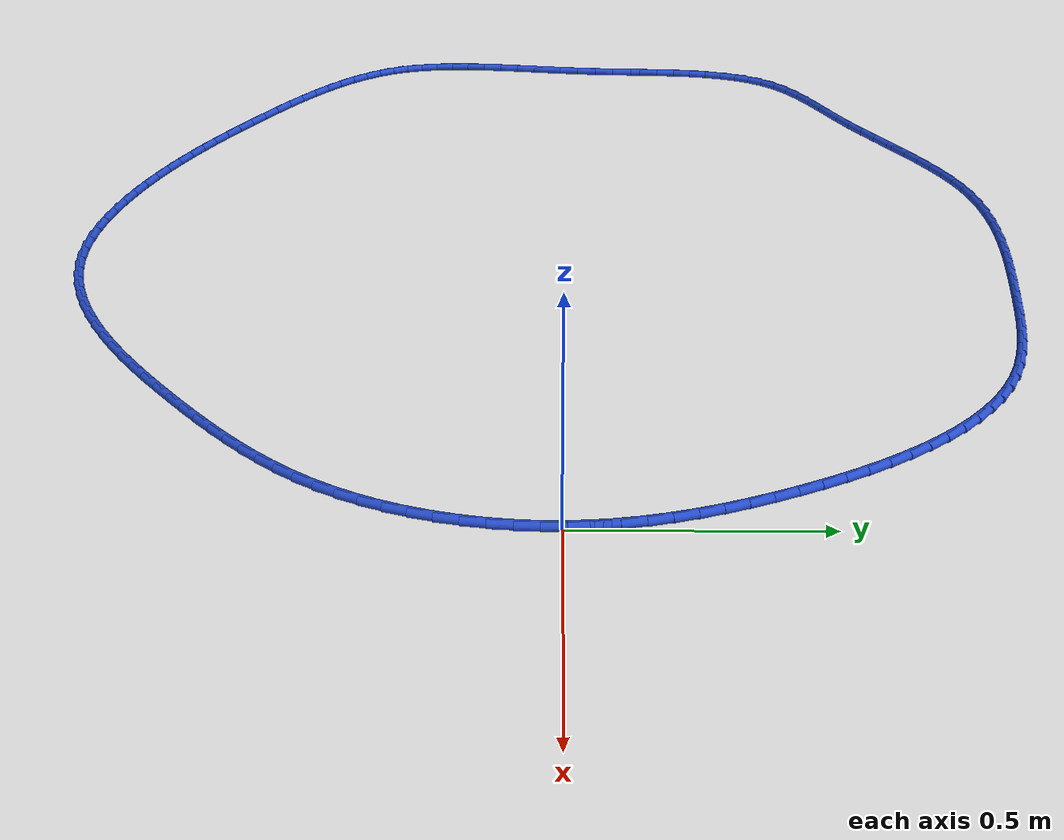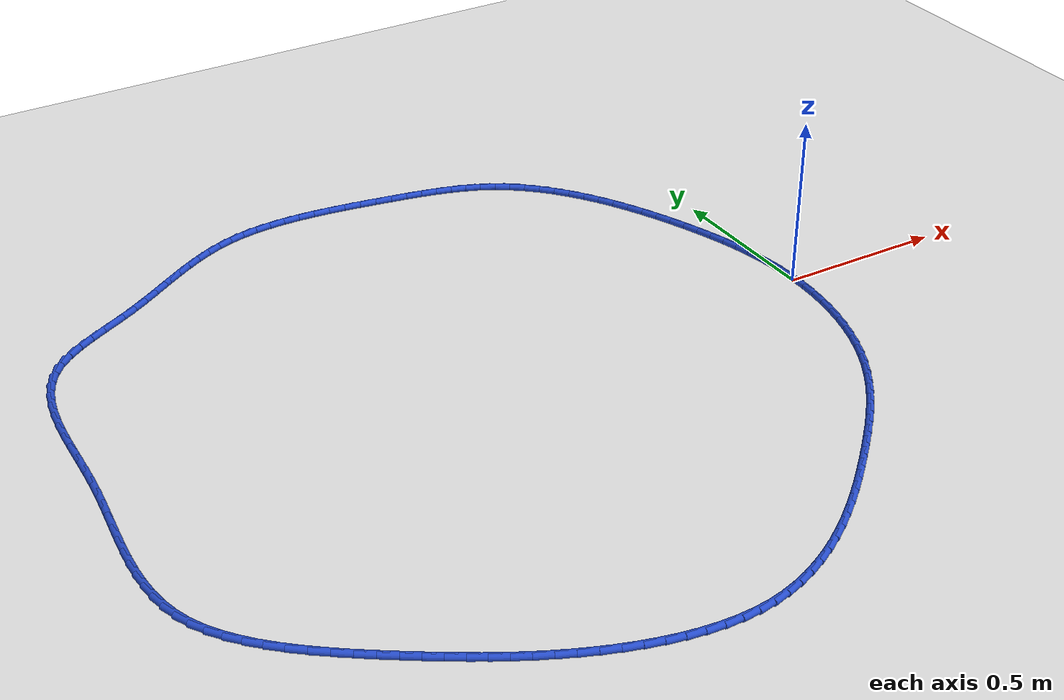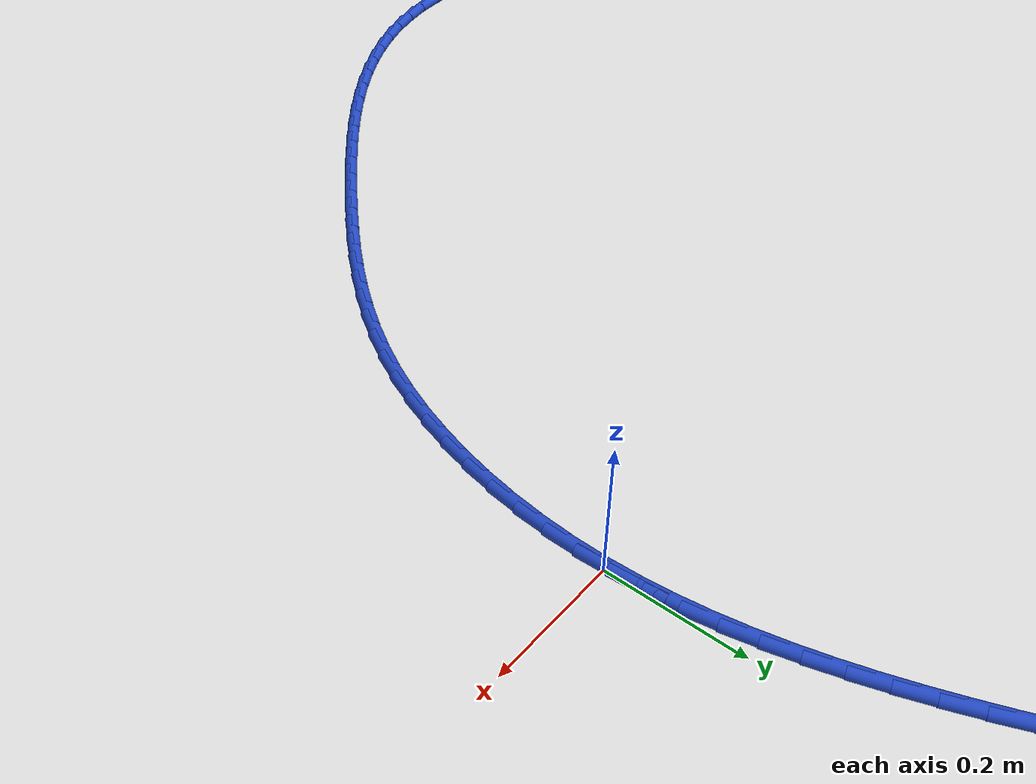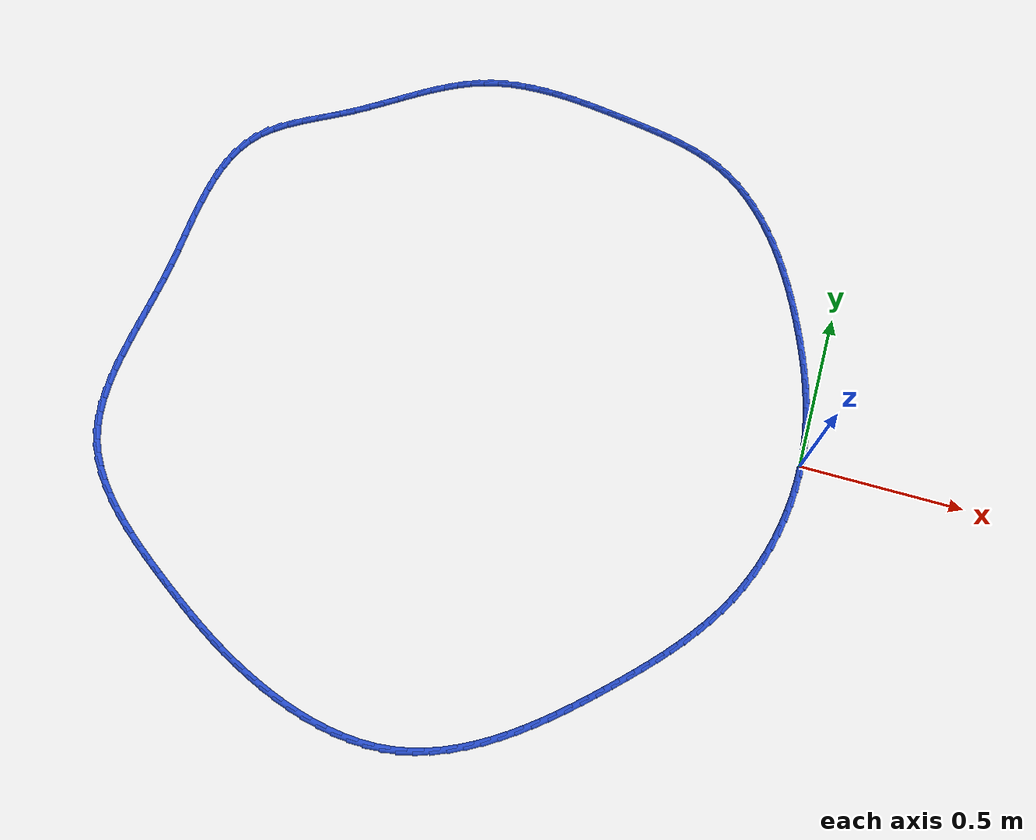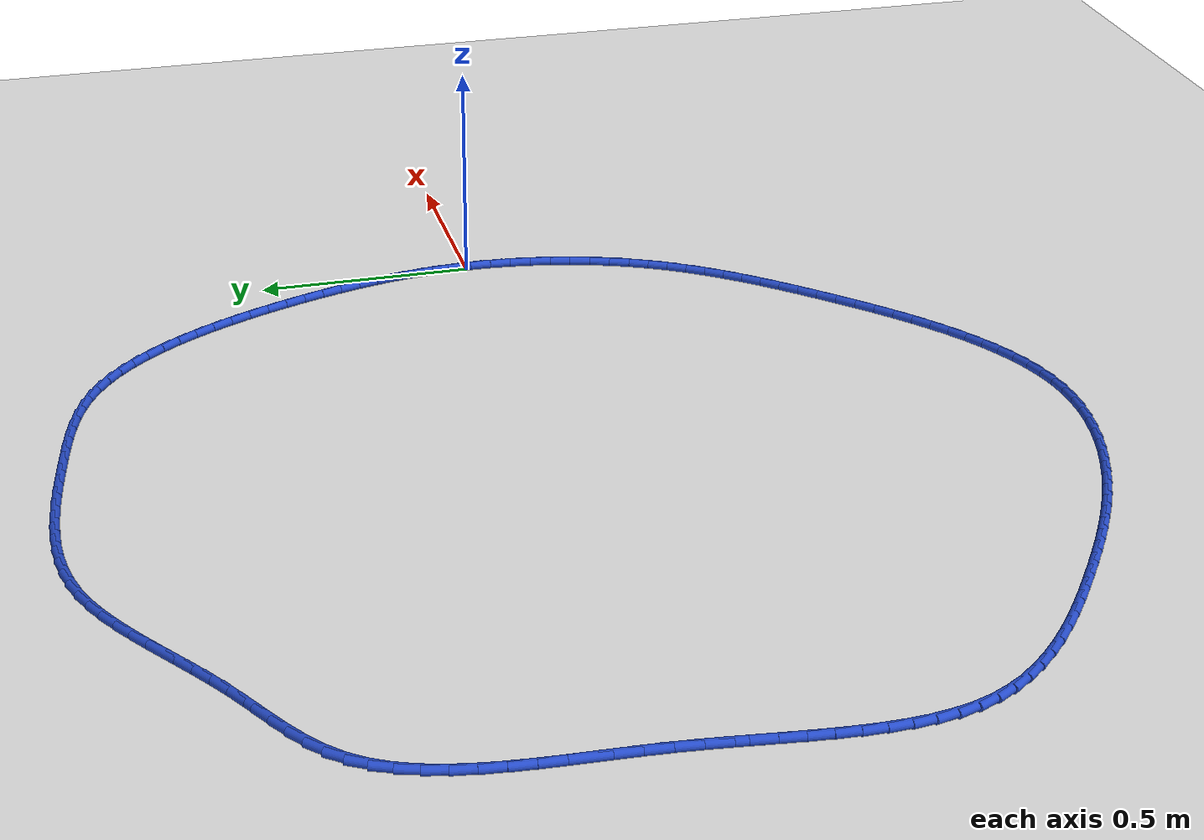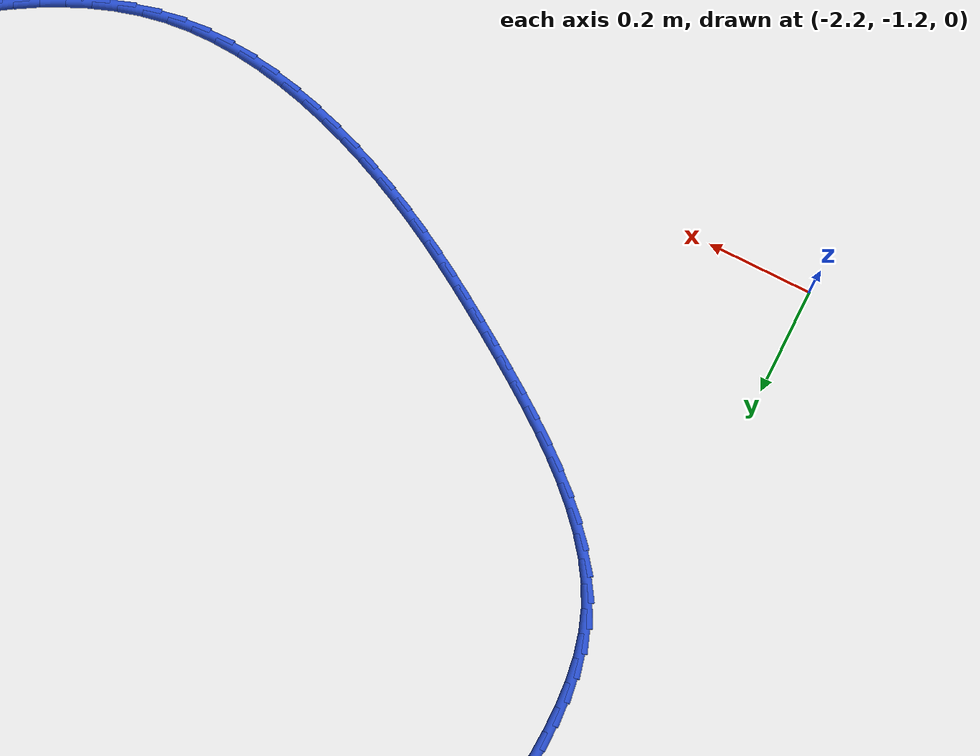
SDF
<sdf version="1.6">
 <world name="default">
  <light name="sun" type="directional">
   <pose>0 0 10 0 -0 0</pose>
   <diffuse>0.8 0.8 0.8 1</diffuse>
   <specular>0.2 0.2 0.2 1</specular>
   <attenuation>
    <range>1000</range>
    <constant>0.9</constant>
    <linear>0.01</linear>
    <quadratic>0.001</quadratic>
   </attenuation>
   <direction>-0.5 0.1 -0.9</direction>
  </light>
  <model name="ground_plane">
   <static>1</static>
   <link name="link">
    <collision name="collision">
     <geometry><plane><normal>0 0 1</normal><size>100 100</size></plane></geometry>
     <surface><friction><ode><mu>100</mu><mu2>50</mu2></ode></friction></surface>
    </collision>
    <visual name="visual">
     <cast_shadows>0</cast_shadows>
     <geometry><plane><normal>0 0 1</normal><size>100 100</size></plane></geometry>
     <material>
      <script><uri>file://media/materials/scripts/gazebo.material</uri><name>Gazebo/WhiteGlow</name></script>
     </material>
    </visual>
   </link>
  </model>
  <gravity>0 0 -9.8</gravity>
  <magnetic_field>6e-06 2.3e-05 -4.2e-05</magnetic_field>
  <atmosphere type="adiabatic"/>
  <physics name="default_physics" default="0" type="ode">
   <max_step_size>0.001</max_step_size>
   <real_time_factor>1</real_time_factor>
   <real_time_update_rate>1000</real_time_update_rate>
  </physics>
  <scene><ambient>0.4 0.4 0.4 1</ambient><background>0.7 0.7 0.7 1</background><shadows>1</shadows></scene>
  <spherical_coordinates>
   <surface_model>EARTH_WGS84</surface_model>
   <latitude_deg>0</latitude_deg>
   <longitude_deg>0</longitude_deg>
   <elevation>0</elevation>
   <heading_deg>0</heading_deg>
  </spherical_coordinates>
  <model name="line">
   <link name="link_0">
    <pose>2.949029909160572e-17 1.3877787807814457e-17 0.01 0 1.57 -1.5270500790770785</pose>
    <collision name="collision">
     <geometry><cylinder><radius>0.01</radius><length>0.08</length></cylinder></geometry>
    </collision>
    <visual name="visual">
     <material>
      <script><name>Gazebo/Blue</name><uri>file://media/materials/scripts/gazebo.material</uri></script>
     </material>
     <geometry><cylinder><radius>0.01</radius><length>0.08</length></cylinder></geometry>
    </visual>
   </link>
   <link name="link_1">
    <pose>-0.0021080150234855937 0.04815659022169293 0.01 0 1.57 -1.4753095987433837</pose>
    <collision name="collision">
     <geometry><cylinder><radius>0.01</radius><length>0.08</length></cylinder></geometry>
    </collision>
    <visual name="visual">
     <material>
      <script><name>Gazebo/Blue</name><uri>file://media/materials/scripts/gazebo.material</uri></script>
     </material>
     <geometry><cylinder><radius>0.01</radius><length>0.08</length></cylinder></geometry>
    </visual>
   </link>
   <link name="link_2">
    <pose>-0.006684725116972691 0.09594115684310281 0.01 0 1.57 -1.4264951042731515</pose>
    <collision name="collision">
     <geometry><cylinder><radius>0.01</radius><length>0.08</length></cylinder></geometry>
    </collision>
    <visual name="visual">
     <material>
      <script><name>Gazebo/Blue</name><uri>file://media/materials/scripts/gazebo.material</uri></script>
     </material>
     <geometry><cylinder><radius>0.01</radius><length>0.08</length></cylinder></geometry>
    </visual>
   </link>
   <link name="link_3">
    <pose>-0.013582654966851319 0.1434111987764339 0.01 0 1.57 -1.3809663778536763</pose>
    <collision name="collision">
     <geometry><cylinder><radius>0.01</radius><length>0.08</length></cylinder></geometry>
    </collision>
    <visual name="visual">
     <material>
      <script><name>Gazebo/Blue</name><uri>file://media/materials/scripts/gazebo.material</uri></script>
     </material>
     <geometry><cylinder><radius>0.01</radius><length>0.08</length></cylinder></geometry>
    </visual>
   </link>
   <link name="link_4">
    <pose>-0.022654329259511566 0.1906242149338905 0.01 0 1.57 -1.3389813049151889</pose>
    <collision name="collision">
     <geometry><cylinder><radius>0.01</radius><length>0.08</length></cylinder></geometry>
    </collision>
    <visual name="visual">
     <material>
      <script><name>Gazebo/Blue</name><uri>file://media/materials/scripts/gazebo.material</uri></script>
     </material>
     <geometry><cylinder><radius>0.01</radius><length>0.08</length></cylinder></geometry>
    </visual>
   </link>
   <link name="link_5">
    <pose>-0.03375227268134352 0.23763770422767705 0.01 0 1.57 -1.3007036057564132</pose>
    <collision name="collision">
     <geometry><cylinder><radius>0.01</radius><length>0.08</length></cylinder></geometry>
    </collision>
    <visual name="visual">
     <material>
      <script><name>Gazebo/Blue</name><uri>file://media/materials/scripts/gazebo.material</uri></script>
     </material>
     <geometry><cylinder><radius>0.01</radius><length>0.08</length></cylinder></geometry>
    </visual>
   </link>
   <link name="link_6">
    <pose>-0.046729009918737276 0.2845091655699978 0.01 0 1.57 -1.2662155867814395</pose>
    <collision name="collision">
     <geometry><cylinder><radius>0.01</radius><length>0.08</length></cylinder></geometry>
    </collision>
    <visual name="visual">
     <material>
      <script><name>Gazebo/Blue</name><uri>file://media/materials/scripts/gazebo.material</uri></script>
     </material>
     <geometry><cylinder><radius>0.01</radius><length>0.08</length></cylinder></geometry>
    </visual>
   </link>
   <link name="link_7">
    <pose>-0.061437065658082886 0.331296097873057 0.01 0 1.57 -1.2355333233967374</pose>
    <collision name="collision">
     <geometry><cylinder><radius>0.01</radius><length>0.08</length></cylinder></geometry>
    </collision>
    <visual name="visual">
     <material>
      <script><name>Gazebo/Blue</name><uri>file://media/materials/scripts/gazebo.material</uri></script>
     </material>
     <geometry><cylinder><radius>0.01</radius><length>0.08</length></cylinder></geometry>
    </visual>
   </link>
   <link name="link_8">
    <pose>-0.07772896458577044 0.37805600004905904 0.01 0 1.57 -1.208622172362613</pose>
    <collision name="collision">
     <geometry><cylinder><radius>0.01</radius><length>0.08</length></cylinder></geometry>
    </collision>
    <visual name="visual">
     <material>
      <script><name>Gazebo/Blue</name><uri>file://media/materials/scripts/gazebo.material</uri></script>
     </material>
     <geometry><cylinder><radius>0.01</radius><length>0.08</length></cylinder></geometry>
    </visual>
   </link>
   <link name="link_9">
    <pose>-0.09545723138819004 0.4248463710102083 0.01 0 1.57 -1.1848216344786682</pose>
    <collision name="collision">
     <geometry><cylinder><radius>0.01</radius><length>0.08</length></cylinder></geometry>
    </collision>
    <visual name="visual">
     <material>
      <script><name>Gazebo/Blue</name><uri>file://media/materials/scripts/gazebo.material</uri></script>
     </material>
     <geometry><cylinder><radius>0.01</radius><length>0.08</length></cylinder></geometry>
    </visual>
   </link>
   <link name="link_10">
    <pose>-0.11449365346020324 0.4716928927452237 0.01 0 1.57 -1.1597349410565683</pose>
    <collision name="collision">
     <geometry><cylinder><radius>0.01</radius><length>0.08</length></cylinder></geometry>
    </collision>
    <visual name="visual">
     <material>
      <script><name>Gazebo/Blue</name><uri>file://media/materials/scripts/gazebo.material</uri></script>
     </material>
     <geometry><cylinder><radius>0.01</radius><length>0.08</length></cylinder></geometry>
    </visual>
   </link>
   <link name="link_11">
    <pose>-0.13484921044014098 0.5183913382989808 0.01 0 1.57 -1.1312293684521706</pose>
    <collision name="collision">
     <geometry><cylinder><radius>0.01</radius><length>0.08</length></cylinder></geometry>
    </collision>
    <visual name="visual">
     <material>
      <script><name>Gazebo/Blue</name><uri>file://media/materials/scripts/gazebo.material</uri></script>
     </material>
     <geometry><cylinder><radius>0.01</radius><length>0.08</length></cylinder></geometry>
    </visual>
   </link>
   <link name="link_12">
    <pose>-0.15659604868870441 0.5646364493931437 0.01 0 1.57 -1.098960488393815</pose>
    <collision name="collision">
     <geometry><cylinder><radius>0.01</radius><length>0.08</length></cylinder></geometry>
    </collision>
    <visual name="visual">
     <material>
      <script><name>Gazebo/Blue</name><uri>file://media/materials/scripts/gazebo.material</uri></script>
     </material>
     <geometry><cylinder><radius>0.01</radius><length>0.08</length></cylinder></geometry>
    </visual>
   </link>
   <link name="link_13">
    <pose>-0.1798065778946938 0.610122532800679 0.01 0 1.57 -1.0625271897896644</pose>
    <collision name="collision">
     <geometry><cylinder><radius>0.01</radius><length>0.08</length></cylinder></geometry>
    </collision>
    <visual name="visual">
     <material>
      <script><name>Gazebo/Blue</name><uri>file://media/materials/scripts/gazebo.material</uri></script>
     </material>
     <geometry><cylinder><radius>0.01</radius><length>0.08</length></cylinder></geometry>
    </visual>
   </link>
   <link name="link_14">
    <pose>-0.20455320774690908 0.6545438952945523 0.01 0 1.57 -1.0214654885212713</pose>
    <collision name="collision">
     <geometry><cylinder><radius>0.01</radius><length>0.08</length></cylinder></geometry>
    </collision>
    <visual name="visual">
     <material>
      <script><name>Gazebo/Blue</name><uri>file://media/materials/scripts/gazebo.material</uri></script>
     </material>
     <geometry><cylinder><radius>0.01</radius><length>0.08</length></cylinder></geometry>
    </visual>
   </link>
   <link name="link_15">
    <pose>-0.23090834793415044 0.6975948436477297 0.01 0 1.57 -0.9752548873377626</pose>
    <collision name="collision">
     <geometry><cylinder><radius>0.01</radius><length>0.08</length></cylinder></geometry>
    </collision>
    <visual name="visual">
     <material>
      <script><name>Gazebo/Blue</name><uri>file://media/materials/scripts/gazebo.material</uri></script>
     </material>
     <geometry><cylinder><radius>0.01</radius><length>0.08</length></cylinder></geometry>
    </visual>
   </link>
   <link name="link_16">
    <pose>-0.2589444081452181 0.7389696846331771 0.01 0 1.57 -0.9233329919966909</pose>
    <collision name="collision">
     <geometry><cylinder><radius>0.01</radius><length>0.08</length></cylinder></geometry>
    </collision>
    <visual name="visual">
     <material>
      <script><name>Gazebo/Blue</name><uri>file://media/materials/scripts/gazebo.material</uri></script>
     </material>
     <geometry><cylinder><radius>0.01</radius><length>0.08</length></cylinder></geometry>
    </visual>
   </link>
   <link name="link_17">
    <pose>-0.288733798068912 0.7783627250238605 0.01 0 1.57 -0.8651235100521042</pose>
    <collision name="collision">
     <geometry><cylinder><radius>0.01</radius><length>0.08</length></cylinder></geometry>
    </collision>
    <visual name="visual">
     <material>
      <script><name>Gazebo/Blue</name><uri>file://media/materials/scripts/gazebo.material</uri></script>
     </material>
     <geometry><cylinder><radius>0.01</radius><length>0.08</length></cylinder></geometry>
    </visual>
   </link>
   <link name="link_18">
    <pose>-0.32034892739403226 0.815468271592746 0.01 0 1.57 -0.8000839393693102</pose>
    <collision name="collision">
     <geometry><cylinder><radius>0.01</radius><length>0.08</length></cylinder></geometry>
    </collision>
    <visual name="visual">
     <material>
      <script><name>Gazebo/Blue</name><uri>file://media/materials/scripts/gazebo.material</uri></script>
     </material>
     <geometry><cylinder><radius>0.01</radius><length>0.08</length></cylinder></geometry>
    </visual>
   </link>
   <link name="link_19">
    <pose>-0.3538622058093792 0.8499806311128 0.01 0 1.57 -0.7277792586374734</pose>
    <collision name="collision">
     <geometry><cylinder><radius>0.01</radius><length>0.08</length></cylinder></geometry>
    </collision>
    <visual name="visual">
     <material>
      <script><name>Gazebo/Blue</name><uri>file://media/materials/scripts/gazebo.material</uri></script>
     </material>
     <geometry><cylinder><radius>0.01</radius><length>0.08</length></cylinder></geometry>
    </visual>
   </link>
   <link name="link_20">
    <pose>-0.38934604300375286 0.8815941103569879 0.01 0 1.57 -0.6479849452834543</pose>
    <collision name="collision">
     <geometry><cylinder><radius>0.01</radius><length>0.08</length></cylinder></geometry>
    </collision>
    <visual name="visual">
     <material>
      <script><name>Gazebo/Blue</name><uri>file://media/materials/scripts/gazebo.material</uri></script>
     </material>
     <geometry><cylinder><radius>0.01</radius><length>0.08</length></cylinder></geometry>
    </visual>
   </link>
   <link name="link_21">
    <pose>-0.4268728486659534 0.9100030160982759 0.01 0 1.57 -0.5608142688628595</pose>
    <collision name="collision">
     <geometry><cylinder><radius>0.01</radius><length>0.08</length></cylinder></geometry>
    </collision>
    <visual name="visual">
     <material>
      <script><name>Gazebo/Blue</name><uri>file://media/materials/scripts/gazebo.material</uri></script>
     </material>
     <geometry><cylinder><radius>0.01</radius><length>0.08</length></cylinder></geometry>
    </visual>
   </link>
   <link name="link_22">
    <pose>-0.46651503248478066 0.9349016551096299 0.01 0 1.57 -0.46835802269086085</pose>
    <collision name="collision">
     <geometry><cylinder><radius>0.01</radius><length>0.08</length></cylinder></geometry>
    </collision>
    <visual name="visual">
     <material>
      <script><name>Gazebo/Blue</name><uri>file://media/materials/scripts/gazebo.material</uri></script>
     </material>
     <geometry><cylinder><radius>0.01</radius><length>0.08</length></cylinder></geometry>
    </visual>
   </link>
   <link name="link_23">
    <pose>-0.5083179618457496 0.9560498390531825 0.01 0 1.57 -0.3838558486477021</pose>
    <collision name="collision">
     <geometry><cylinder><radius>0.01</radius><length>0.08</length></cylinder></geometry>
    </collision>
    <visual name="visual">
     <material>
      <script><name>Gazebo/Blue</name><uri>file://media/materials/scripts/gazebo.material</uri></script>
     </material>
     <geometry><cylinder><radius>0.01</radius><length>0.08</length></cylinder></geometry>
    </visual>
   </link>
   <link name="link_24">
    <pose>-0.5521085843262832 0.9737364604600268 0.01 0 1.57 -0.3138845367107355</pose>
    <collision name="collision">
     <geometry><cylinder><radius>0.01</radius><length>0.08</length></cylinder></geometry>
    </collision>
    <visual name="visual">
     <material>
      <script><name>Gazebo/Blue</name><uri>file://media/materials/scripts/gazebo.material</uri></script>
     </material>
     <geometry><cylinder><radius>0.01</radius><length>0.08</length></cylinder></geometry>
    </visual>
   </link>
   <link name="link_25">
    <pose>-0.5976081853539015 0.9885063585291625 0.01 0 1.57 -0.2583179083406088</pose>
    <collision name="collision">
     <geometry><cylinder><radius>0.01</radius><length>0.08</length></cylinder></geometry>
    </collision>
    <visual name="visual">
     <material>
      <script><name>Gazebo/Blue</name><uri>file://media/materials/scripts/gazebo.material</uri></script>
     </material>
     <geometry><cylinder><radius>0.01</radius><length>0.08</length></cylinder></geometry>
    </visual>
   </link>
   <link name="link_26">
    <pose>-0.6445373609561406 1.0009060424012792 0.01 0 1.57 -0.21652099601731747</pose>
    <collision name="collision">
     <geometry><cylinder><radius>0.01</radius><length>0.08</length></cylinder></geometry>
    </collision>
    <visual name="visual">
     <material>
      <script><name>Gazebo/Blue</name><uri>file://media/materials/scripts/gazebo.material</uri></script>
     </material>
     <geometry><cylinder><radius>0.01</radius><length>0.08</length></cylinder></geometry>
    </visual>
   </link>
   <link name="link_27">
    <pose>-0.6926167071605357 1.011482021217066 0.01 0 1.57 -0.18772766723072412</pose>
    <collision name="collision">
     <geometry><cylinder><radius>0.01</radius><length>0.08</length></cylinder></geometry>
    </collision>
    <visual name="visual">
     <material>
      <script><name>Gazebo/Blue</name><uri>file://media/materials/scripts/gazebo.material</uri></script>
     </material>
     <geometry><cylinder><radius>0.01</radius><length>0.08</length></cylinder></geometry>
    </visual>
   </link>
   <link name="link_28">
    <pose>-0.7415668199946233 1.020780804117212 0.01 0 1.57 -0.17125389188216888</pose>
    <collision name="collision">
     <geometry><cylinder><radius>0.01</radius><length>0.08</length></cylinder></geometry>
    </collision>
    <visual name="visual">
     <material>
      <script><name>Gazebo/Blue</name><uri>file://media/materials/scripts/gazebo.material</uri></script>
     </material>
     <geometry><cylinder><radius>0.01</radius><length>0.08</length></cylinder></geometry>
    </visual>
   </link>
   <link name="link_29">
    <pose>-0.7911082954859383 1.0293489002424057 0.01 0 1.57 -0.16448188469074282</pose>
    <collision name="collision">
     <geometry><cylinder><radius>0.01</radius><length>0.08</length></cylinder></geometry>
    </collision>
    <visual name="visual">
     <material>
      <script><name>Gazebo/Blue</name><uri>file://media/materials/scripts/gazebo.material</uri></script>
     </material>
     <geometry><cylinder><radius>0.01</radius><length>0.08</length></cylinder></geometry>
    </visual>
   </link>
   <link name="link_30">
    <pose>-0.8409772888123374 1.0376262269663048 0.01 0 1.57 -0.15540796066716067</pose>
    <collision name="collision">
     <geometry><cylinder><radius>0.01</radius><length>0.08</length></cylinder></geometry>
    </collision>
    <visual name="visual">
     <material>
      <script><name>Gazebo/Blue</name><uri>file://media/materials/scripts/gazebo.material</uri></script>
     </material>
     <geometry><cylinder><radius>0.01</radius><length>0.08</length></cylinder></geometry>
    </visual>
   </link>
   <link name="link_31">
    <pose>-0.8909960724420577 1.0454627340895108 0.01 0 1.57 -0.1398761797422882</pose>
    <collision name="collision">
     <geometry><cylinder><radius>0.01</radius><length>0.08</length></cylinder></geometry>
    </collision>
    <visual name="visual">
     <material>
      <script><name>Gazebo/Blue</name><uri>file://media/materials/scripts/gazebo.material</uri></script>
     </material>
     <geometry><cylinder><radius>0.01</radius><length>0.08</length></cylinder></geometry>
    </visual>
   </link>
   <link name="link_32">
    <pose>-0.9410165468222182 1.0525053976924983 0.01 0 1.57 -0.11766382904063616</pose>
    <collision name="collision">
     <geometry><cylinder><radius>0.01</radius><length>0.08</length></cylinder></geometry>
    </collision>
    <visual name="visual">
     <material>
      <script><name>Gazebo/Blue</name><uri>file://media/materials/scripts/gazebo.material</uri></script>
     </material>
     <geometry><cylinder><radius>0.01</radius><length>0.08</length></cylinder></geometry>
    </visual>
   </link>
   <link name="link_33">
    <pose>-0.9908906396216842 1.0584010073665093 0.01 0 1.57 -0.08842106904402151</pose>
    <collision name="collision">
     <geometry><cylinder><radius>0.01</radius><length>0.08</length></cylinder></geometry>
    </collision>
    <visual name="visual">
     <material>
      <script><name>Gazebo/Blue</name><uri>file://media/materials/scripts/gazebo.material</uri></script>
     </material>
     <geometry><cylinder><radius>0.01</radius><length>0.08</length></cylinder></geometry>
    </visual>
   </link>
   <link name="link_34">
    <pose>-1.040470278509321 1.062796352702786 0.01 0 1.57 -0.05168408826343095</pose>
    <collision name="collision">
     <geometry><cylinder><radius>0.01</radius><length>0.08</length></cylinder></geometry>
    </collision>
    <visual name="visual">
     <material>
      <script><name>Gazebo/Blue</name><uri>file://media/materials/scripts/gazebo.material</uri></script>
     </material>
     <geometry><cylinder><radius>0.01</radius><length>0.08</length></cylinder></geometry>
    </visual>
   </link>
   <link name="link_35">
    <pose>-1.0896073911539925 1.0653382232925686 0.01 0 1.57 -0.0069043084739173</pose>
    <collision name="collision">
     <geometry><cylinder><radius>0.01</radius><length>0.08</length></cylinder></geometry>
    </collision>
    <visual name="visual">
     <material>
      <script><name>Gazebo/Blue</name><uri>file://media/materials/scripts/gazebo.material</uri></script>
     </material>
     <geometry><cylinder><radius>0.01</radius><length>0.08</length></cylinder></geometry>
    </visual>
   </link>
   <link name="link_36">
    <pose>-1.1381539052245655 1.0656734087271 0.01 0 1.57 0.04650087163829302</pose>
    <collision name="collision">
     <geometry><cylinder><radius>0.01</radius><length>0.08</length></cylinder></geometry>
    </collision>
    <visual name="visual">
     <material>
      <script><name>Gazebo/Blue</name><uri>file://media/materials/scripts/gazebo.material</uri></script>
     </material>
     <geometry><cylinder><radius>0.01</radius><length>0.08</length></cylinder></geometry>
    </visual>
   </link>
   <link name="link_37">
    <pose>-1.1859617483899045 1.0634486985976215 0.01 0 1.57 0.10906454384270917</pose>
    <collision name="collision">
     <geometry><cylinder><radius>0.01</radius><length>0.08</length></cylinder></geometry>
    </collision>
    <visual name="visual">
     <material>
      <script><name>Gazebo/Blue</name><uri>file://media/materials/scripts/gazebo.material</uri></script>
     </material>
     <geometry><cylinder><radius>0.01</radius><length>0.08</length></cylinder></geometry>
    </visual>
   </link>
   <link name="link_38">
    <pose>-1.2328828483188747 1.0583108824953742 0.01 0 1.57 0.18114365162302634</pose>
    <collision name="collision">
     <geometry><cylinder><radius>0.01</radius><length>0.08</length></cylinder></geometry>
    </collision>
    <visual name="visual">
     <material>
      <script><name>Gazebo/Blue</name><uri>file://media/materials/scripts/gazebo.material</uri></script>
     </material>
     <geometry><cylinder><radius>0.01</radius><length>0.08</length></cylinder></geometry>
    </visual>
   </link>
   <link name="link_39">
    <pose>-1.2787691326803412 1.0499067500116002 0.01 0 1.57 0.26274653824986105</pose>
    <collision name="collision">
     <geometry><cylinder><radius>0.01</radius><length>0.08</length></cylinder></geometry>
    </collision>
    <visual name="visual">
     <material>
      <script><name>Gazebo/Blue</name><uri>file://media/materials/scripts/gazebo.material</uri></script>
     </material>
     <geometry><cylinder><radius>0.01</radius><length>0.08</length></cylinder></geometry>
    </visual>
   </link>
   <link name="link_40">
    <pose>-1.3234725404830396 1.0378831156690278 0.01 0 1.57 0.34911365693599217</pose>
    <collision name="collision">
     <geometry><cylinder><radius>0.01</radius><length>0.08</length></cylinder></geometry>
    </collision>
    <visual name="visual">
     <material>
      <script><name>Gazebo/Blue</name><uri>file://media/materials/scripts/gazebo.material</uri></script>
     </material>
     <geometry><cylinder><radius>0.01</radius><length>0.08</length></cylinder></geometry>
    </visual>
   </link>
   <link name="link_41">
    <pose>-1.3669260557082155 1.0220649769526504 0.01 0 1.57 0.42475879441147996</pose>
    <collision name="collision">
     <geometry><cylinder><radius>0.01</radius><length>0.08</length></cylinder></geometry>
    </collision>
    <visual name="visual">
     <material>
      <script><name>Gazebo/Blue</name><uri>file://media/materials/scripts/gazebo.material</uri></script>
     </material>
     <geometry><cylinder><radius>0.01</radius><length>0.08</length></cylinder></geometry>
    </visual>
   </link>
   <link name="link_42">
    <pose>-1.409337882827586 1.002882422579519 0.01 0 1.57 0.4858780325012394</pose>
    <collision name="collision">
     <geometry><cylinder><radius>0.01</radius><length>0.08</length></cylinder></geometry>
    </collision>
    <visual name="visual">
     <material>
      <script><name>Gazebo/Blue</name><uri>file://media/materials/scripts/gazebo.material</uri></script>
     </material>
     <geometry><cylinder><radius>0.01</radius><length>0.08</length></cylinder></geometry>
    </visual>
   </link>
   <link name="link_43">
    <pose>-1.450974593402284 0.9808938653387228 0.01 0 1.57 0.5325024177753516</pose>
    <collision name="collision">
     <geometry><cylinder><radius>0.01</radius><length>0.08</length></cylinder></geometry>
    </collision>
    <visual name="visual">
     <material>
      <script><name>Gazebo/Blue</name><uri>file://media/materials/scripts/gazebo.material</uri></script>
     </material>
     <geometry><cylinder><radius>0.01</radius><length>0.08</length></cylinder></geometry>
    </visual>
   </link>
   <link name="link_44">
    <pose>-1.492102758993443 0.956657718019353 0.01 0 1.57 0.5651057505240626</pose>
    <collision name="collision">
     <geometry><cylinder><radius>0.01</radius><length>0.08</length></cylinder></geometry>
    </collision>
    <visual name="visual">
     <material>
      <script><name>Gazebo/Blue</name><uri>file://media/materials/scripts/gazebo.material</uri></script>
     </material>
     <geometry><cylinder><radius>0.01</radius><length>0.08</length></cylinder></geometry>
    </visual>
   </link>
   <link name="link_45">
    <pose>-1.5329889511621957 0.9307323934105002 0.01 0 1.57 0.5843083403184012</pose>
    <collision name="collision">
     <geometry><cylinder><radius>0.01</radius><length>0.08</length></cylinder></geometry>
    </collision>
    <visual name="visual">
     <material>
      <script><name>Gazebo/Blue</name><uri>file://media/materials/scripts/gazebo.material</uri></script>
     </material>
     <geometry><cylinder><radius>0.01</radius><length>0.08</length></cylinder></geometry>
    </visual>
   </link>
   <link name="link_46">
    <pose>-1.5738997414696754 0.9036763043012541 0.01 0 1.57 0.5906940597236352</pose>
    <collision name="collision">
     <geometry><cylinder><radius>0.01</radius><length>0.08</length></cylinder></geometry>
    </collision>
    <visual name="visual">
     <material>
      <script><name>Gazebo/Blue</name><uri>file://media/materials/scripts/gazebo.material</uri></script>
     </material>
     <geometry><cylinder><radius>0.01</radius><length>0.08</length></cylinder></geometry>
    </visual>
   </link>
   <link name="link_47">
    <pose>-1.615101701477015 0.8760478634807065 0.01 0 1.57 0.5847225386798085</pose>
    <collision name="collision">
     <geometry><cylinder><radius>0.01</radius><length>0.08</length></cylinder></geometry>
    </collision>
    <visual name="visual">
     <material>
      <script><name>Gazebo/Blue</name><uri>file://media/materials/scripts/gazebo.material</uri></script>
     </material>
     <geometry><cylinder><radius>0.01</radius><length>0.08</length></cylinder></geometry>
    </visual>
   </link>
   <link name="link_48">
    <pose>-1.6568614027453479 0.8484054837379469 0.01 0 1.57 0.5667122993684152</pose>
    <collision name="collision">
     <geometry><cylinder><radius>0.01</radius><length>0.08</length></cylinder></geometry>
    </collision>
    <visual name="visual">
     <material>
      <script><name>Gazebo/Blue</name><uri>file://media/materials/scripts/gazebo.material</uri></script>
     </material>
     <geometry><cylinder><radius>0.01</radius><length>0.08</length></cylinder></geometry>
    </visual>
   </link>
   <link name="link_49">
    <pose>-1.6994454168358064 0.8213075778620663 0.01 0 1.57 0.5369062151635484</pose>
    <collision name="collision">
     <geometry><cylinder><radius>0.01</radius><length>0.08</length></cylinder></geometry>
    </collision>
    <visual name="visual">
     <material>
      <script><name>Gazebo/Blue</name><uri>file://media/materials/scripts/gazebo.material</uri></script>
     </material>
     <geometry><cylinder><radius>0.01</radius><length>0.08</length></cylinder></geometry>
    </visual>
   </link>
   <link name="link_50">
    <pose>-1.7431192681825576 0.7953115055704685 0.01 0 1.57 0.5054243779346007</pose>
    <collision name="collision">
     <geometry><cylinder><radius>0.01</radius><length>0.08</length></cylinder></geometry>
    </collision>
    <visual name="visual">
     <material>
      <script><name>Gazebo/Blue</name><uri>file://media/materials/scripts/gazebo.material</uri></script>
     </material>
     <geometry><cylinder><radius>0.01</radius><length>0.08</length></cylinder></geometry>
    </visual>
   </link>
   <link name="link_51">
    <pose>-1.7877759512402733 0.7705999816843135 0.01 0 1.57 0.4965302506560757</pose>
    <collision name="collision">
     <geometry><cylinder><radius>0.01</radius><length>0.08</length></cylinder></geometry>
    </collision>
    <visual name="visual">
     <material>
      <script><name>Gazebo/Blue</name><uri>file://media/materials/scripts/gazebo.material</uri></script>
     </material>
     <geometry><cylinder><radius>0.01</radius><length>0.08</length></cylinder></geometry>
    </visual>
   </link>
   <link name="link_52">
    <pose>-1.8323872787598143 0.7464293096140207 0.01 0 1.57 0.5141889459597901</pose>
    <collision name="collision">
     <geometry><cylinder><radius>0.01</radius><length>0.08</length></cylinder></geometry>
    </collision>
    <visual name="visual">
     <material>
      <script><name>Gazebo/Blue</name><uri>file://media/materials/scripts/gazebo.material</uri></script>
     </material>
     <geometry><cylinder><radius>0.01</radius><length>0.08</length></cylinder></geometry>
    </visual>
   </link>
   <link name="link_53">
    <pose>-1.8757851592793289 0.7219150942970263 0.01 0 1.57 0.5604719948466994</pose>
    <collision name="collision">
     <geometry><cylinder><radius>0.01</radius><length>0.08</length></cylinder></geometry>
    </collision>
    <visual name="visual">
     <material>
      <script><name>Gazebo/Blue</name><uri>file://media/materials/scripts/gazebo.material</uri></script>
     </material>
     <geometry><cylinder><radius>0.01</radius><length>0.08</length></cylinder></geometry>
    </visual>
   </link>
   <link name="link_54">
    <pose>-1.9168015013369646 0.6961729406707647 0.01 0 1.57 0.6392935034693884</pose>
    <collision name="collision">
     <geometry><cylinder><radius>0.01</radius><length>0.08</length></cylinder></geometry>
    </collision>
    <visual name="visual">
     <material>
      <script><name>Gazebo/Blue</name><uri>file://media/materials/scripts/gazebo.material</uri></script>
     </material>
     <geometry><cylinder><radius>0.01</radius><length>0.08</length></cylinder></geometry>
    </visual>
   </link>
   <link name="link_55">
    <pose>-1.9542682134708709 0.6683184536726715 0.01 0 1.57 0.755567876876201</pose>
    <collision name="collision">
     <geometry><cylinder><radius>0.01</radius><length>0.08</length></cylinder></geometry>
    </collision>
    <visual name="visual">
     <material>
      <script><name>Gazebo/Blue</name><uri>file://media/materials/scripts/gazebo.material</uri></script>
     </material>
     <geometry><cylinder><radius>0.01</radius><length>0.08</length></cylinder></geometry>
    </visual>
   </link>
   <link name="link_56">
    <pose>-1.9870172042191947 0.6374672382401821 0.01 0 1.57 0.9059892556153714</pose>
    <collision name="collision">
     <geometry><cylinder><radius>0.01</radius><length>0.08</length></cylinder></geometry>
    </collision>
    <visual name="visual">
     <material>
      <script><name>Gazebo/Blue</name><uri>file://media/materials/scripts/gazebo.material</uri></script>
     </material>
     <geometry><cylinder><radius>0.01</radius><length>0.08</length></cylinder></geometry>
    </visual>
   </link>
   <link name="link_57">
    <pose>-2.0141143510012847 0.6028973360371297 0.01 0 1.57 1.053774161450152</pose>
    <collision name="collision">
     <geometry><cylinder><radius>0.01</radius><length>0.08</length></cylinder></geometry>
    </collision>
    <visual name="visual">
     <material>
      <script><name>Gazebo/Blue</name><uri>file://media/materials/scripts/gazebo.material</uri></script>
     </material>
     <geometry><cylinder><radius>0.01</radius><length>0.08</length></cylinder></geometry>
    </visual>
   </link>
   <link name="link_58">
    <pose>-2.0358234224170753 0.5647184442917905 0.01 0 1.57 1.181949540184219</pose>
    <collision name="collision">
     <geometry><cylinder><radius>0.01</radius><length>0.08</length></cylinder></geometry>
    </collision>
    <visual name="visual">
     <material>
      <script><name>Gazebo/Blue</name><uri>file://media/materials/scripts/gazebo.material</uri></script>
     </material>
     <geometry><cylinder><radius>0.01</radius><length>0.08</length></cylinder></geometry>
    </visual>
   </link>
   <link name="link_59">
    <pose>-2.052790530355083 0.5233057083204016 0.01 0 1.57 1.2878568737318823</pose>
    <collision name="collision">
     <geometry><cylinder><radius>0.01</radius><length>0.08</length></cylinder></geometry>
    </collision>
    <visual name="visual">
     <material>
      <script><name>Gazebo/Blue</name><uri>file://media/materials/scripts/gazebo.material</uri></script>
     </material>
     <geometry><cylinder><radius>0.01</radius><length>0.08</length></cylinder></geometry>
    </visual>
   </link>
   <link name="link_60">
    <pose>-2.065661953196362 0.4790343890293742 0.01 0 1.57 1.371939230554957</pose>
    <collision name="collision">
     <geometry><cylinder><radius>0.01</radius><length>0.08</length></cylinder></geometry>
    </collision>
    <visual name="visual">
     <material>
      <script><name>Gazebo/Blue</name><uri>file://media/materials/scripts/gazebo.material</uri></script>
     </material>
     <geometry><cylinder><radius>0.01</radius><length>0.08</length></cylinder></geometry>
    </visual>
   </link>
   <link name="link_61">
    <pose>-2.0750839693219714 0.4322797473251194 0.01 0 1.57 1.436156944812052</pose>
    <collision name="collision">
     <geometry><cylinder><radius>0.01</radius><length>0.08</length></cylinder></geometry>
    </collision>
    <visual name="visual">
     <material>
      <script><name>Gazebo/Blue</name><uri>file://media/materials/scripts/gazebo.material</uri></script>
     </material>
     <geometry><cylinder><radius>0.01</radius><length>0.08</length></cylinder></geometry>
    </visual>
   </link>
   <link name="link_62">
    <pose>-2.0817028571129654 0.38341704411404876 0.01 0 1.57 1.482833498422117</pose>
    <collision name="collision">
     <geometry><cylinder><radius>0.01</radius><length>0.08</length></cylinder></geometry>
    </collision>
    <visual name="visual">
     <material>
      <script><name>Gazebo/Blue</name><uri>file://media/materials/scripts/gazebo.material</uri></script>
     </material>
     <geometry><cylinder><radius>0.01</radius><length>0.08</length></cylinder></geometry>
    </visual>
   </link>
   <link name="link_63">
    <pose>-2.086164894950404 0.33282154030257316 0.01 0 1.57 1.5140470584801262</pose>
    <collision name="collision">
     <geometry><cylinder><radius>0.01</radius><length>0.08</length></cylinder></geometry>
    </collision>
    <visual name="visual">
     <material>
      <script><name>Gazebo/Blue</name><uri>file://media/materials/scripts/gazebo.material</uri></script>
     </material>
     <geometry><cylinder><radius>0.01</radius><length>0.08</length></cylinder></geometry>
    </visual>
   </link>
   <link name="link_64">
    <pose>-2.0891163612153423 0.28086849679710446 0.01 0 1.57 1.531387999802183</pose>
    <collision name="collision">
     <geometry><cylinder><radius>0.01</radius><length>0.08</length></cylinder></geometry>
    </collision>
    <visual name="visual">
     <material>
      <script><name>Gazebo/Blue</name><uri>file://media/materials/scripts/gazebo.material</uri></script>
     </material>
     <geometry><cylinder><radius>0.01</radius><length>0.08</length></cylinder></geometry>
    </visual>
   </link>
   <link name="link_65">
    <pose>-2.0912035342888378 0.22793317450405343 0.01 0 1.57 1.5359005882772656</pose>
    <collision name="collision">
     <geometry><cylinder><radius>0.01</radius><length>0.08</length></cylinder></geometry>
    </collision>
    <visual name="visual">
     <material>
      <script><name>Gazebo/Blue</name><uri>file://media/materials/scripts/gazebo.material</uri></script>
     </material>
     <geometry><cylinder><radius>0.01</radius><length>0.08</length></cylinder></geometry>
    </visual>
   </link>
   <link name="link_66">
    <pose>-2.093072692551947 0.17439083432983082 0.01 0 1.57 1.5280987148735161</pose>
    <collision name="collision">
     <geometry><cylinder><radius>0.01</radius><length>0.08</length></cylinder></geometry>
    </collision>
    <visual name="visual">
     <material>
      <script><name>Gazebo/Blue</name><uri>file://media/materials/scripts/gazebo.material</uri></script>
     </material>
     <geometry><cylinder><radius>0.01</radius><length>0.08</length></cylinder></geometry>
    </visual>
   </link>
   <link name="link_67">
    <pose>-2.095370114385727 0.12061673718084891 0.01 0 1.57 1.508068709074419</pose>
    <collision name="collision">
     <geometry><cylinder><radius>0.01</radius><length>0.08</length></cylinder></geometry>
    </collision>
    <visual name="visual">
     <material>
      <script><name>Gazebo/Blue</name><uri>file://media/materials/scripts/gazebo.material</uri></script>
     </material>
     <geometry><cylinder><radius>0.01</radius><length>0.08</length></cylinder></geometry>
    </visual>
   </link>
   <link name="link_68">
    <pose>-2.0987387020951562 0.06698536260825867 0.01 0 1.57 1.4826363617765324</pose>
    <collision name="collision">
     <geometry><cylinder><radius>0.01</radius><length>0.08</length></cylinder></geometry>
    </collision>
    <visual name="visual">
     <material>
      <script><name>Gazebo/Blue</name><uri>file://media/materials/scripts/gazebo.material</uri></script>
     </material>
     <geometry><cylinder><radius>0.01</radius><length>0.08</length></cylinder></geometry>
    </visual>
   </link>
   <link name="link_69">
    <pose>-2.1034411916397686 0.013783204890832809 0.01 0 1.57 1.4652987616519582</pose>
    <collision name="collision">
     <geometry><cylinder><radius>0.01</radius><length>0.08</length></cylinder></geometry>
    </collision>
    <visual name="visual">
     <material>
      <script><name>Gazebo/Blue</name><uri>file://media/materials/scripts/gazebo.material</uri></script>
     </material>
     <geometry><cylinder><radius>0.01</radius><length>0.08</length></cylinder></geometry>
    </visual>
   </link>
   <link name="link_70">
    <pose>-2.109016750965219 -0.03887070346182893 0.01 0 1.57 1.4577025907081003</pose>
    <collision name="collision">
     <geometry><cylinder><radius>0.01</radius><length>0.08</length></cylinder></geometry>
    </collision>
    <visual name="visual">
     <material>
      <script><name>Gazebo/Blue</name><uri>file://media/materials/scripts/gazebo.material</uri></script>
     </material>
     <geometry><cylinder><radius>0.01</radius><length>0.08</length></cylinder></geometry>
    </visual>
   </link>
   <link name="link_71">
    <pose>-2.114923439792665 -0.09087610153658539 0.01 0 1.57 1.4601256677248313</pose>
    <collision name="collision">
     <geometry><cylinder><radius>0.01</radius><length>0.08</length></cylinder></geometry>
    </collision>
    <visual name="visual">
     <material>
      <script><name>Gazebo/Blue</name><uri>file://media/materials/scripts/gazebo.material</uri></script>
     </material>
     <geometry><cylinder><radius>0.01</radius><length>0.08</length></cylinder></geometry>
    </visual>
   </link>
   <link name="link_72">
    <pose>-2.120619317843265 -0.14213272842029662 0.01 0 1.57 1.4730457235114607</pose>
    <collision name="collision">
     <geometry><cylinder><radius>0.01</radius><length>0.08</length></cylinder></geometry>
    </collision>
    <visual name="visual">
     <material>
      <script><name>Gazebo/Blue</name><uri>file://media/materials/scripts/gazebo.material</uri></script>
     </material>
     <geometry><cylinder><radius>0.01</radius><length>0.08</length></cylinder></geometry>
    </visual>
   </link>
   <link name="link_73">
    <pose>-2.1255624448381787 -0.19254032319982312 0.01 0 1.57 1.4971617871678637</pose>
    <collision name="collision">
     <geometry><cylinder><radius>0.01</radius><length>0.08</length></cylinder></geometry>
    </collision>
    <visual name="visual">
     <material>
      <script><name>Gazebo/Blue</name><uri>file://media/materials/scripts/gazebo.material</uri></script>
     </material>
     <geometry><cylinder><radius>0.01</radius><length>0.08</length></cylinder></geometry>
    </visual>
   </link>
   <link name="link_74">
    <pose>-2.129210880498562 -0.24199862496202293 0.01 0 1.57 1.5333865847660677</pose>
    <collision name="collision">
     <geometry><cylinder><radius>0.01</radius><length>0.08</length></cylinder></geometry>
    </collision>
    <visual name="visual">
     <material>
      <script><name>Gazebo/Blue</name><uri>file://media/materials/scripts/gazebo.material</uri></script>
     </material>
     <geometry><cylinder><radius>0.01</radius><length>0.08</length></cylinder></geometry>
    </visual>
   </link>
   <link name="link_75">
    <pose>-2.131022684545576 -0.29040737279375656 0.01 0 1.57 -1.5588040823788425</pose>
    <collision name="collision">
     <geometry><cylinder><radius>0.01</radius><length>0.08</length></cylinder></geometry>
    </collision>
    <visual name="visual">
     <material>
      <script><name>Gazebo/Blue</name><uri>file://media/materials/scripts/gazebo.material</uri></script>
     </material>
     <geometry><cylinder><radius>0.01</radius><length>0.08</length></cylinder></geometry>
    </visual>
   </link>
   <link name="link_76">
    <pose>-2.130455916700377 -0.3376663057818838 0.01 0 1.57 -1.4951451370231805</pose>
    <collision name="collision">
     <geometry><cylinder><radius>0.01</radius><length>0.08</length></cylinder></geometry>
    </collision>
    <visual name="visual">
     <material>
      <script><name>Gazebo/Blue</name><uri>file://media/materials/scripts/gazebo.material</uri></script>
     </material>
     <geometry><cylinder><radius>0.01</radius><length>0.08</length></cylinder></geometry>
    </visual>
   </link>
   <link name="link_77">
    <pose>-2.126968636684125 -0.38367516301326415 0.01 0 1.57 -1.4164152090351878</pose>
    <collision name="collision">
     <geometry><cylinder><radius>0.01</radius><length>0.08</length></cylinder></geometry>
    </collision>
    <visual name="visual">
     <material>
      <script><name>Gazebo/Blue</name><uri>file://media/materials/scripts/gazebo.material</uri></script>
     </material>
     <geometry><cylinder><radius>0.01</radius><length>0.08</length></cylinder></geometry>
    </visual>
   </link>
   <link name="link_78">
    <pose>-2.1200189042179773 -0.42833368357475804 0.01 0 1.57 -1.3225063331948141</pose>
    <collision name="collision">
     <geometry><cylinder><radius>0.01</radius><length>0.08</length></cylinder></geometry>
    </collision>
    <visual name="visual">
     <material>
      <script><name>Gazebo/Blue</name><uri>file://media/materials/scripts/gazebo.material</uri></script>
     </material>
     <geometry><cylinder><radius>0.01</radius><length>0.08</length></cylinder></geometry>
    </visual>
   </link>
   <link name="link_79">
    <pose>-2.1090647790230928 -0.47154160655322375 0.01 0 1.57 -1.2145734001211714</pose>
    <collision name="collision">
     <geometry><cylinder><radius>0.01</radius><length>0.08</length></cylinder></geometry>
    </collision>
    <visual name="visual">
     <material>
      <script><name>Gazebo/Blue</name><uri>file://media/materials/scripts/gazebo.material</uri></script>
     </material>
     <geometry><cylinder><radius>0.01</radius><length>0.08</length></cylinder></geometry>
    </visual>
   </link>
   <link name="link_80">
    <pose>-2.0935643208206303 -0.5131986710355217 0.01 0 1.57 -1.09858608623336</pose>
    <collision name="collision">
     <geometry><cylinder><radius>0.01</radius><length>0.08</length></cylinder></geometry>
    </collision>
    <visual name="visual">
     <material>
      <script><name>Gazebo/Blue</name><uri>file://media/materials/scripts/gazebo.material</uri></script>
     </material>
     <geometry><cylinder><radius>0.01</radius><length>0.08</length></cylinder></geometry>
    </visual>
   </link>
   <link name="link_81">
    <pose>-2.073119520883767 -0.5532276812550262 0.01 0 1.57 -0.9930406484010695</pose>
    <collision name="collision">
     <geometry><cylinder><radius>0.01</radius><length>0.08</length></cylinder></geometry>
    </collision>
    <visual name="visual">
     <material>
      <script><name>Gazebo/Blue</name><uri>file://media/materials/scripts/gazebo.material</uri></script>
     </material>
     <geometry><cylinder><radius>0.01</radius><length>0.08</length></cylinder></geometry>
    </visual>
   </link>
   <link name="link_82">
    <pose>-2.0480579460356987 -0.5916677155082605 0.01 0 1.57 -0.9030074856389123</pose>
    <collision name="collision">
     <geometry><cylinder><radius>0.01</radius><length>0.08</length></cylinder></geometry>
    </collision>
    <visual name="visual">
     <material>
      <script><name>Gazebo/Blue</name><uri>file://media/materials/scripts/gazebo.material</uri></script>
     </material>
     <geometry><cylinder><radius>0.01</radius><length>0.08</length></cylinder></geometry>
    </visual>
   </link>
   <link name="link_83">
    <pose>-2.0189352869341857 -0.6285944091189847 0.01 0 1.57 -0.8273752394986924</pose>
    <collision name="collision">
     <geometry><cylinder><radius>0.01</radius><length>0.08</length></cylinder></geometry>
    </collision>
    <visual name="visual">
     <material>
      <script><name>Gazebo/Blue</name><uri>file://media/materials/scripts/gazebo.material</uri></script>
     </material>
     <geometry><cylinder><radius>0.01</radius><length>0.08</length></cylinder></geometry>
    </visual>
   </link>
   <link name="link_84">
    <pose>-1.986307317270731 -0.6640834107171851 0.01 0 1.57 -0.7645911894296382</pose>
    <collision name="collision">
     <geometry><cylinder><radius>0.01</radius><length>0.08</length></cylinder></geometry>
    </collision>
    <visual name="visual">
     <material>
      <script><name>Gazebo/Blue</name><uri>file://media/materials/scripts/gazebo.material</uri></script>
     </material>
     <geometry><cylinder><radius>0.01</radius><length>0.08</length></cylinder></geometry>
    </visual>
   </link>
   <link name="link_85">
    <pose>-1.9507298107368356 -0.6982103689328466 0.01 0 1.57 -0.7130690652214379</pose>
    <collision name="collision">
     <geometry><cylinder><radius>0.01</radius><length>0.08</length></cylinder></geometry>
    </collision>
    <visual name="visual">
     <material>
      <script><name>Gazebo/Blue</name><uri>file://media/materials/scripts/gazebo.material</uri></script>
     </material>
     <geometry><cylinder><radius>0.01</radius><length>0.08</length></cylinder></geometry>
    </visual>
   </link>
   <link name="link_86">
    <pose>-1.9127585410240004 -0.7310509323959541 0.01 0 1.57 -0.6713992311692655</pose>
    <collision name="collision">
     <geometry><cylinder><radius>0.01</radius><length>0.08</length></cylinder></geometry>
    </collision>
    <visual name="visual">
     <material>
      <script><name>Gazebo/Blue</name><uri>file://media/materials/scripts/gazebo.material</uri></script>
     </material>
     <geometry><cylinder><radius>0.01</radius><length>0.08</length></cylinder></geometry>
    </visual>
   </link>
   <link name="link_87">
    <pose>-1.8729492818237268 -0.7626807497364934 0.01 0 1.57 -0.6384374612555435</pose>
    <collision name="collision">
     <geometry><cylinder><radius>0.01</radius><length>0.08</length></cylinder></geometry>
    </collision>
    <visual name="visual">
     <material>
      <script><name>Gazebo/Blue</name><uri>file://media/materials/scripts/gazebo.material</uri></script>
     </material>
     <geometry><cylinder><radius>0.01</radius><length>0.08</length></cylinder></geometry>
    </visual>
   </link>
   <link name="link_88">
    <pose>-1.8318578068275178 -0.7931754695844486 0.01 0 1.57 -0.6133328508145751</pose>
    <collision name="collision">
     <geometry><cylinder><radius>0.01</radius><length>0.08</length></cylinder></geometry>
    </collision>
    <visual name="visual">
     <material>
      <script><name>Gazebo/Blue</name><uri>file://media/materials/scripts/gazebo.material</uri></script>
     </material>
     <geometry><cylinder><radius>0.01</radius><length>0.08</length></cylinder></geometry>
    </visual>
   </link>
   <link name="link_89">
    <pose>-1.7900398897268737 -0.8226107405698052 0.01 0 1.57 -0.5955337732191922</pose>
    <collision name="collision">
     <geometry><cylinder><radius>0.01</radius><length>0.08</length></cylinder></geometry>
    </collision>
    <visual name="visual">
     <material>
      <script><name>Gazebo/Blue</name><uri>file://media/materials/scripts/gazebo.material</uri></script>
     </material>
     <geometry><cylinder><radius>0.01</radius><length>0.08</length></cylinder></geometry>
    </visual>
   </link>
   <link name="link_90">
    <pose>-1.748051304213296 -0.8510622113225482 0.01 0 1.57 -0.5842450995692731</pose>
    <collision name="collision">
     <geometry><cylinder><radius>0.01</radius><length>0.08</length></cylinder></geometry>
    </collision>
    <visual name="visual">
     <material>
      <script><name>Gazebo/Blue</name><uri>file://media/materials/scripts/gazebo.material</uri></script>
     </material>
     <geometry><cylinder><radius>0.01</radius><length>0.08</length></cylinder></geometry>
    </visual>
   </link>
   <link name="link_91">
    <pose>-1.706406506679395 -0.8785999460265086 0.01 0 1.57 -0.5732049060419735</pose>
    <collision name="collision">
     <geometry><cylinder><radius>0.01</radius><length>0.08</length></cylinder></geometry>
    </collision>
    <visual name="visual">
     <material>
      <script><name>Gazebo/Blue</name><uri>file://media/materials/scripts/gazebo.material</uri></script>
     </material>
     <geometry><cylinder><radius>0.01</radius><length>0.08</length></cylinder></geometry>
    </visual>
   </link>
   <link name="link_92">
    <pose>-1.6651506532471734 -0.9052305782405219 0.01 0 1.57 -0.5584300908195082</pose>
    <collision name="collision">
     <geometry><cylinder><radius>0.01</radius><length>0.08</length></cylinder></geometry>
    </collision>
    <visual name="visual">
     <material>
      <script><name>Gazebo/Blue</name><uri>file://media/materials/scripts/gazebo.material</uri></script>
     </material>
     <geometry><cylinder><radius>0.01</radius><length>0.08</length></cylinder></geometry>
    </visual>
   </link>
   <link name="link_93">
    <pose>-1.6240312744871561 -0.9309205144536223 0.01 0 1.57 -0.5399012512269443</pose>
    <collision name="collision">
     <geometry><cylinder><radius>0.01</radius><length>0.08</length></cylinder></geometry>
    </collision>
    <visual name="visual">
     <material>
      <script><name>Gazebo/Blue</name><uri>file://media/materials/scripts/gazebo.material</uri></script>
     </material>
     <geometry><cylinder><radius>0.01</radius><length>0.08</length></cylinder></geometry>
    </visual>
   </link>
   <link name="link_94">
    <pose>-1.582791166820843 -0.955635521287258 0.01 0 1.57 -0.5177703478051598</pose>
    <collision name="collision">
     <geometry><cylinder><radius>0.01</radius><length>0.08</length></cylinder></geometry>
    </collision>
    <visual name="visual">
     <material>
      <script><name>Gazebo/Blue</name><uri>file://media/materials/scripts/gazebo.material</uri></script>
     </material>
     <geometry><cylinder><radius>0.01</radius><length>0.08</length></cylinder></geometry>
    </visual>
   </link>
   <link name="link_95">
    <pose>-1.5411731266697324 -0.9793413653628765 0.01 0 1.57 -0.49230220709086614</pose>
    <collision name="collision">
     <geometry><cylinder><radius>0.01</radius><length>0.08</length></cylinder></geometry>
    </collision>
    <visual name="visual">
     <material>
      <script><name>Gazebo/Blue</name><uri>file://media/materials/scripts/gazebo.material</uri></script>
     </material>
     <geometry><cylinder><radius>0.01</radius><length>0.08</length></cylinder></geometry>
    </visual>
   </link>
   <link name="link_96">
    <pose>-1.4989199504553243 -1.0020038133019242 0.01 0 1.57 -0.4638712085479937</pose>
    <collision name="collision">
     <geometry><cylinder><radius>0.01</radius><length>0.08</length></cylinder></geometry>
    </collision>
    <visual name="visual">
     <material>
      <script><name>Gazebo/Blue</name><uri>file://media/materials/scripts/gazebo.material</uri></script>
     </material>
     <geometry><cylinder><radius>0.01</radius><length>0.08</length></cylinder></geometry>
    </visual>
   </link>
   <link name="link_97">
    <pose>-1.455774434599119 -1.0235886317258494 0.01 0 1.57 -0.43294335362747244</pose>
    <collision name="collision">
     <geometry><cylinder><radius>0.01</radius><length>0.08</length></cylinder></geometry>
    </collision>
    <visual name="visual">
     <material>
      <script><name>Gazebo/Blue</name><uri>file://media/materials/scripts/gazebo.material</uri></script>
     </material>
     <geometry><cylinder><radius>0.01</radius><length>0.08</length></cylinder></geometry>
    </visual>
   </link>
   <link name="link_98">
    <pose>-1.411482765635323 -1.0440597223734103 0.01 0 1.57 -0.3996310521360238</pose>
    <collision name="collision">
     <geometry><cylinder><radius>0.01</radius><length>0.08</length></cylinder></geometry>
    </collision>
    <visual name="visual">
     <material>
      <script><name>Gazebo/Blue</name><uri>file://media/materials/scripts/gazebo.material</uri></script>
     </material>
     <geometry><cylinder><radius>0.01</radius><length>0.08</length></cylinder></geometry>
    </visual>
   </link>
   <link name="link_99">
    <pose>-1.3659713381320435 -1.063281855517334 0.01 0 1.57 -0.3632738160665019</pose>
    <collision name="collision">
     <geometry><cylinder><radius>0.01</radius><length>0.08</length></cylinder></geometry>
    </collision>
    <visual name="visual">
     <material>
      <script><name>Gazebo/Blue</name><uri>file://media/materials/scripts/gazebo.material</uri></script>
     </material>
     <geometry><cylinder><radius>0.01</radius><length>0.08</length></cylinder></geometry>
    </visual>
   </link>
   <link name="link_100">
    <pose>-1.3194332886292257 -1.0809730681124785 0.01 0 1.57 -0.32333017129916647</pose>
    <collision name="collision">
     <geometry><cylinder><radius>0.01</radius><length>0.08</length></cylinder></geometry>
    </collision>
    <visual name="visual">
     <material>
      <script><name>Gazebo/Blue</name><uri>file://media/materials/scripts/gazebo.material</uri></script>
     </material>
     <geometry><cylinder><radius>0.01</radius><length>0.08</length></cylinder></geometry>
    </visual>
   </link>
   <link name="link_101">
    <pose>-1.272083289329398 -1.0968395504620416 0.01 0 1.57 -0.27923884316806485</pose>
    <collision name="collision">
     <geometry><cylinder><radius>0.01</radius><length>0.08</length></cylinder></geometry>
    </collision>
    <visual name="visual">
     <material>
      <script><name>Gazebo/Blue</name><uri>file://media/materials/scripts/gazebo.material</uri></script>
     </material>
     <geometry><cylinder><radius>0.01</radius><length>0.08</length></cylinder></geometry>
    </visual>
   </link>
   <link name="link_102">
    <pose>-1.2241360124350873 -1.1105874928692232 0.01 0 1.57 -0.23038191614448647</pose>
    <collision name="collision">
     <geometry><cylinder><radius>0.01</radius><length>0.08</length></cylinder></geometry>
    </collision>
    <visual name="visual">
     <material>
      <script><name>Gazebo/Blue</name><uri>file://media/materials/scripts/gazebo.material</uri></script>
     </material>
     <geometry><cylinder><radius>0.01</radius><length>0.08</length></cylinder></geometry>
    </visual>
   </link>
   <link name="link_103">
    <pose>-1.1758061301488212 -1.121923085637221 0.01 0 1.57 -0.17609151982380267</pose>
    <collision name="collision">
     <geometry><cylinder><radius>0.01</radius><length>0.08</length></cylinder></geometry>
    </collision>
    <visual name="visual">
     <material>
      <script><name>Gazebo/Blue</name><uri>file://media/materials/scripts/gazebo.material</uri></script>
     </material>
     <geometry><cylinder><radius>0.01</radius><length>0.08</length></cylinder></geometry>
    </visual>
   </link>
   <link name="link_104">
    <pose>-1.127308314673127 -1.1305525190692356 0.01 0 1.57 -0.11566998766903314</pose>
    <collision name="collision">
     <geometry><cylinder><radius>0.01</radius><length>0.08</length></cylinder></geometry>
    </collision>
    <visual name="visual">
     <material>
      <script><name>Gazebo/Blue</name><uri>file://media/materials/scripts/gazebo.material</uri></script>
     </material>
     <geometry><cylinder><radius>0.01</radius><length>0.08</length></cylinder></geometry>
    </visual>
   </link>
   <link name="link_105">
    <pose>-1.0788572382105337 -1.136181983468464 0.01 0 1.57 -0.048430700434600155</pose>
    <collision name="collision">
     <geometry><cylinder><radius>0.01</radius><length>0.08</length></cylinder></geometry>
    </collision>
    <visual name="visual">
     <material>
      <script><name>Gazebo/Blue</name><uri>file://media/materials/scripts/gazebo.material</uri></script>
     </material>
     <geometry><cylinder><radius>0.01</radius><length>0.08</length></cylinder></geometry>
    </visual>
   </link>
   <link name="link_106">
    <pose>-1.0306675729635673 -1.1385176691381056 0.01 0 1.57 0.0262318515326128</pose>
    <collision name="collision">
     <geometry><cylinder><radius>0.01</radius><length>0.08</length></cylinder></geometry>
    </collision>
    <visual name="visual">
     <material>
      <script><name>Gazebo/Blue</name><uri>file://media/materials/scripts/gazebo.material</uri></script>
     </material>
     <geometry><cylinder><radius>0.01</radius><length>0.08</length></cylinder></geometry>
    </visual>
   </link>
   <link name="link_107">
    <pose>-0.9829539911347567 -1.1372657663813597 0.01 0 1.57 0.1087213182173005</pose>
    <collision name="collision">
     <geometry><cylinder><radius>0.01</radius><length>0.08</length></cylinder></geometry>
    </collision>
    <visual name="visual">
     <material>
      <script><name>Gazebo/Blue</name><uri>file://media/materials/scripts/gazebo.material</uri></script>
     </material>
     <geometry><cylinder><radius>0.01</radius><length>0.08</length></cylinder></geometry>
    </visual>
   </link>
   <link name="link_108">
    <pose>-0.9359309147166178 -1.1321331163751465 0.01 0 1.57 0.19549393749243196</pose>
    <collision name="collision">
     <geometry><cylinder><radius>0.01</radius><length>0.08</length></cylinder></geometry>
    </collision>
    <visual name="visual">
     <material>
      <script><name>Gazebo/Blue</name><uri>file://media/materials/scripts/gazebo.material</uri></script>
     </material>
     <geometry><cylinder><radius>0.01</radius><length>0.08</length></cylinder></geometry>
    </visual>
   </link>
   <link name="link_109">
    <pose>-0.8897505726713586 -1.1229883436279113 0.01 0 1.57 0.2775598739028718</pose>
    <collision name="collision">
     <geometry><cylinder><radius>0.01</radius><length>0.08</length></cylinder></geometry>
    </collision>
    <visual name="visual">
     <material>
      <script><name>Gazebo/Blue</name><uri>file://media/materials/scripts/gazebo.material</uri></script>
     </material>
     <geometry><cylinder><radius>0.01</radius><length>0.08</length></cylinder></geometry>
    </visual>
   </link>
   <link name="link_110">
    <pose>-0.8444216460617842 -1.1100734851877894 0.01 0 1.57 0.35298451580189705</pose>
    <collision name="collision">
     <geometry><cylinder><radius>0.01</radius><length>0.08</length></cylinder></geometry>
    </collision>
    <visual name="visual">
     <material>
      <script><name>Gazebo/Blue</name><uri>file://media/materials/scripts/gazebo.material</uri></script>
     </material>
     <geometry><cylinder><radius>0.01</radius><length>0.08</length></cylinder></geometry>
    </visual>
   </link>
   <link name="link_111">
    <pose>-0.7999326287381991 -1.0936830912941238 0.01 0 1.57 0.421407375718957</pose>
    <collision name="collision">
     <geometry><cylinder><radius>0.01</radius><length>0.08</length></cylinder></geometry>
    </collision>
    <visual name="visual">
     <material>
      <script><name>Gazebo/Blue</name><uri>file://media/materials/scripts/gazebo.material</uri></script>
     </material>
     <geometry><cylinder><radius>0.01</radius><length>0.08</length></cylinder></geometry>
    </visual>
   </link>
   <link name="link_112">
    <pose>-0.7562720145509088 -1.074111712186257 0.01 0 1.57 0.48280385996978425</pose>
    <collision name="collision">
     <geometry><cylinder><radius>0.01</radius><length>0.08</length></cylinder></geometry>
    </collision>
    <visual name="visual">
     <material>
      <script><name>Gazebo/Blue</name><uri>file://media/materials/scripts/gazebo.material</uri></script>
     </material>
     <geometry><cylinder><radius>0.01</radius><length>0.08</length></cylinder></geometry>
    </visual>
   </link>
   <link name="link_113">
    <pose>-0.713428297350217 -1.0516538981035304 0.01 0 1.57 0.537382841809601</pose>
    <collision name="collision">
     <geometry><cylinder><radius>0.01</radius><length>0.08</length></cylinder></geometry>
    </collision>
    <visual name="visual">
     <material>
      <script><name>Gazebo/Blue</name><uri>file://media/materials/scripts/gazebo.material</uri></script>
     </material>
     <geometry><cylinder><radius>0.01</radius><length>0.08</length></cylinder></geometry>
    </visual>
   </link>
   <link name="link_114">
    <pose>-0.6713899709864305 -1.0266041992852881 0.01 0 1.57 0.5854929974513385</pose>
    <collision name="collision">
     <geometry><cylinder><radius>0.01</radius><length>0.08</length></cylinder></geometry>
    </collision>
    <visual name="visual">
     <material>
      <script><name>Gazebo/Blue</name><uri>file://media/materials/scripts/gazebo.material</uri></script>
     </material>
     <geometry><cylinder><radius>0.01</radius><length>0.08</length></cylinder></geometry>
    </visual>
   </link>
   <link name="link_115">
    <pose>-0.6301455293098533 -0.999257165970872 0.01 0 1.57 0.6275482575768158</pose>
    <collision name="collision">
     <geometry><cylinder><radius>0.01</radius><length>0.08</length></cylinder></geometry>
    </collision>
    <visual name="visual">
     <material>
      <script><name>Gazebo/Blue</name><uri>file://media/materials/scripts/gazebo.material</uri></script>
     </material>
     <geometry><cylinder><radius>0.01</radius><length>0.08</length></cylinder></geometry>
    </visual>
   </link>
   <link name="link_116">
    <pose>-0.5896834661707908 -0.9699073483996247 0.01 0 1.57 0.6639739813423248</pose>
    <collision name="collision">
     <geometry><cylinder><radius>0.01</radius><length>0.08</length></cylinder></geometry>
    </collision>
    <visual name="visual">
     <material>
      <script><name>Gazebo/Blue</name><uri>file://media/materials/scripts/gazebo.material</uri></script>
     </material>
     <geometry><cylinder><radius>0.01</radius><length>0.08</length></cylinder></geometry>
    </visual>
   </link>
   <link name="link_117">
    <pose>-0.5499922754195471 -0.9388492968108877 0.01 0 1.57 0.6951708807874665</pose>
    <collision name="collision">
     <geometry><cylinder><radius>0.01</radius><length>0.08</length></cylinder></geometry>
    </collision>
    <visual name="visual">
     <material>
      <script><name>Gazebo/Blue</name><uri>file://media/materials/scripts/gazebo.material</uri></script>
     </material>
     <geometry><cylinder><radius>0.01</radius><length>0.08</length></cylinder></geometry>
    </visual>
   </link>
   <link name="link_118">
    <pose>-0.5110604509064287 -0.9063775614440055 0.01 0 1.57 0.7214921825918141</pose>
    <collision name="collision">
     <geometry><cylinder><radius>0.01</radius><length>0.08</length></cylinder></geometry>
    </collision>
    <visual name="visual">
     <material>
      <script><name>Gazebo/Blue</name><uri>file://media/materials/scripts/gazebo.material</uri></script>
     </material>
     <geometry><cylinder><radius>0.01</radius><length>0.08</length></cylinder></geometry>
    </visual>
   </link>
   <link name="link_119">
    <pose>-0.47287648648173963 -0.8727866925383194 0.01 0 1.57 0.7432296180157397</pose>
    <collision name="collision">
     <geometry><cylinder><radius>0.01</radius><length>0.08</length></cylinder></geometry>
    </collision>
    <visual name="visual">
     <material>
      <script><name>Gazebo/Blue</name><uri>file://media/materials/scripts/gazebo.material</uri></script>
     </material>
     <geometry><cylinder><radius>0.01</radius><length>0.08</length></cylinder></geometry>
    </visual>
   </link>
   <link name="link_120">
    <pose>-0.43542887599578517 -0.8383712403331722 0.01 0 1.57 0.7606045722329761</pose>
    <collision name="collision">
     <geometry><cylinder><radius>0.01</radius><length>0.08</length></cylinder></geometry>
    </collision>
    <visual name="visual">
     <material>
      <script><name>Gazebo/Blue</name><uri>file://media/materials/scripts/gazebo.material</uri></script>
     </material>
     <geometry><cylinder><radius>0.01</radius><length>0.08</length></cylinder></geometry>
    </visual>
   </link>
   <link name="link_121">
    <pose>-0.39870611329887035 -0.8034257550679067 0.01 0 1.57 0.7738499170220088</pose>
    <collision name="collision">
     <geometry><cylinder><radius>0.01</radius><length>0.08</length></cylinder></geometry>
    </collision>
    <visual name="visual">
     <material>
      <script><name>Gazebo/Blue</name><uri>file://media/materials/scripts/gazebo.material</uri></script>
     </material>
     <geometry><cylinder><radius>0.01</radius><length>0.08</length></cylinder></geometry>
    </visual>
   </link>
   <link name="link_122">
    <pose>-0.36269850164913825 -0.7682403346428015 0.01 0 1.57 0.786787861958652</pose>
    <collision name="collision">
     <geometry><cylinder><radius>0.01</radius><length>0.08</length></cylinder></geometry>
    </collision>
    <visual name="visual">
     <material>
      <script><name>Gazebo/Blue</name><uri>file://media/materials/scripts/gazebo.material</uri></script>
     </material>
     <geometry><cylinder><radius>0.01</radius><length>0.08</length></cylinder></geometry>
    </visual>
   </link>
   <link name="link_123">
    <pose>-0.32747290248569494 -0.7329166932381316 0.01 0 1.57 0.804577808397292</pose>
    <collision name="collision">
     <geometry><cylinder><radius>0.01</radius><length>0.08</length></cylinder></geometry>
    </collision>
    <visual name="visual">
     <material>
      <script><name>Gazebo/Blue</name><uri>file://media/materials/scripts/gazebo.material</uri></script>
     </material>
     <geometry><cylinder><radius>0.01</radius><length>0.08</length></cylinder></geometry>
    </visual>
   </link>
   <link name="link_124">
    <pose>-0.2931993833181845 -0.6973025898950663 0.01 0 1.57 0.8277119165674608</pose>
    <collision name="collision">
     <geometry><cylinder><radius>0.01</radius><length>0.08</length></cylinder></geometry>
    </collision>
    <visual name="visual">
     <material>
      <script><name>Gazebo/Blue</name><uri>file://media/materials/scripts/gazebo.material</uri></script>
     </material>
     <geometry><cylinder><radius>0.01</radius><length>0.08</length></cylinder></geometry>
    </visual>
   </link>
   <link name="link_125">
    <pose>-0.26005530012772193 -0.6612278491982421 0.01 0 1.57 0.8563041909436947</pose>
    <collision name="collision">
     <geometry><cylinder><radius>0.01</radius><length>0.08</length></cylinder></geometry>
    </collision>
    <visual name="visual">
     <material>
      <script><name>Gazebo/Blue</name><uri>file://media/materials/scripts/gazebo.material</uri></script>
     </material>
     <geometry><cylinder><radius>0.01</radius><length>0.08</length></cylinder></geometry>
    </visual>
   </link>
   <link name="link_126">
    <pose>-0.22821800889542163 -0.6245222957322951 0.01 0 1.57 0.8904248357819515</pose>
    <collision name="collision">
     <geometry><cylinder><radius>0.01</radius><length>0.08</length></cylinder></geometry>
    </collision>
    <visual name="visual">
     <material>
      <script><name>Gazebo/Blue</name><uri>file://media/materials/scripts/gazebo.material</uri></script>
     </material>
     <geometry><cylinder><radius>0.01</radius><length>0.08</length></cylinder></geometry>
    </visual>
   </link>
   <link name="link_127">
    <pose>-0.1978648656023997 -0.5870157540818627 0.01 0 1.57 0.9300727019835326</pose>
    <collision name="collision">
     <geometry><cylinder><radius>0.01</radius><length>0.08</length></cylinder></geometry>
    </collision>
    <visual name="visual">
     <material>
      <script><name>Gazebo/Blue</name><uri>file://media/materials/scripts/gazebo.material</uri></script>
     </material>
     <geometry><cylinder><radius>0.01</radius><length>0.08</length></cylinder></geometry>
    </visual>
   </link>
   <link name="link_128">
    <pose>-0.16917322622977052 -0.5485380488315806 0.01 0 1.57 0.975143030565546</pose>
    <collision name="collision">
     <geometry><cylinder><radius>0.01</radius><length>0.08</length></cylinder></geometry>
    </collision>
    <visual name="visual">
     <material>
      <script><name>Gazebo/Blue</name><uri>file://media/materials/scripts/gazebo.material</uri></script>
     </material>
     <geometry><cylinder><radius>0.01</radius><length>0.08</length></cylinder></geometry>
    </visual>
   </link>
   <link name="link_129">
    <pose>-0.14232044675864916 -0.5089190045660854 0.01 0 1.57 1.0253935984132356</pose>
    <collision name="collision">
     <geometry><cylinder><radius>0.01</radius><length>0.08</length></cylinder></geometry>
    </collision>
    <visual name="visual">
     <material>
      <script><name>Gazebo/Blue</name><uri>file://media/materials/scripts/gazebo.material</uri></script>
     </material>
     <geometry><cylinder><radius>0.01</radius><length>0.08</length></cylinder></geometry>
    </visual>
   </link>
   <link name="link_130">
    <pose>-0.11748388317015057 -0.4679884458700133 0.01 0 1.57 1.0804067441409055</pose>
    <collision name="collision">
     <geometry><cylinder><radius>0.01</radius><length>0.08</length></cylinder></geometry>
    </collision>
    <visual name="visual">
     <material>
      <script><name>Gazebo/Blue</name><uri>file://media/materials/scripts/gazebo.material</uri></script>
     </material>
     <geometry><cylinder><radius>0.01</radius><length>0.08</length></cylinder></geometry>
    </visual>
   </link>
   <link name="link_131">
    <pose>-0.09484071545507244 -0.4255766679907247 0.01 0 1.57 1.1378766607939899</pose>
    <collision name="collision">
     <geometry><cylinder><radius>0.01</radius><length>0.08</length></cylinder></geometry>
    </collision>
    <visual name="visual">
     <material>
      <script><name>Gazebo/Blue</name><uri>file://media/materials/scripts/gazebo.material</uri></script>
     </material>
     <geometry><cylinder><radius>0.01</radius><length>0.08</length></cylinder></geometry>
    </visual>
   </link>
   <link name="link_132">
    <pose>-0.07452724399089868 -0.3816232932709509 0.01 0 1.57 1.1937600956516035</pose>
    <collision name="collision">
     <geometry><cylinder><radius>0.01</radius><length>0.08</length></cylinder></geometry>
    </collision>
    <visual name="visual">
     <material>
      <script><name>Gazebo/Blue</name><uri>file://media/materials/scripts/gazebo.material</uri></script>
     </material>
     <geometry><cylinder><radius>0.01</radius><length>0.08</length></cylinder></geometry>
    </visual>
   </link>
   <link name="link_133">
    <pose>-0.05658674267161009 -0.33631673102592713 0.01 0 1.57 1.2479189738776737</pose>
    <collision name="collision">
     <geometry><cylinder><radius>0.01</radius><length>0.08</length></cylinder></geometry>
    </collision>
    <visual name="visual">
     <material>
      <script><name>Gazebo/Blue</name><uri>file://media/materials/scripts/gazebo.material</uri></script>
     </material>
     <geometry><cylinder><radius>0.01</radius><length>0.08</length></cylinder></geometry>
    </visual>
   </link>
   <link name="link_134">
    <pose>-0.04104961152704746 -0.2898798200103703 0.01 0 1.57 1.3007883373066151</pose>
    <collision name="collision">
     <geometry><cylinder><radius>0.01</radius><length>0.08</length></cylinder></geometry>
    </collision>
    <visual name="visual">
     <material>
      <script><name>Gazebo/Blue</name><uri>file://media/materials/scripts/gazebo.material</uri></script>
     </material>
     <geometry><cylinder><radius>0.01</radius><length>0.08</length></cylinder></geometry>
    </visual>
   </link>
   <link name="link_135">
    <pose>-0.027946250587051375 -0.2425353989789972 0.01 0 1.57 1.3528009004465567</pose>
    <collision name="collision">
     <geometry><cylinder><radius>0.01</radius><length>0.08</length></cylinder></geometry>
    </collision>
    <visual name="visual">
     <material>
      <script><name>Gazebo/Blue</name><uri>file://media/materials/scripts/gazebo.material</uri></script>
     </material>
     <geometry><cylinder><radius>0.01</radius><length>0.08</length></cylinder></geometry>
    </visual>
   </link>
   <link name="link_136">
    <pose>-0.017307059881463017 -0.1945063066865263 0.01 0 1.57 1.404387836492369</pose>
    <collision name="collision">
     <geometry><cylinder><radius>0.01</radius><length>0.08</length></cylinder></geometry>
    </collision>
    <visual name="visual">
     <material>
      <script><name>Gazebo/Blue</name><uri>file://media/materials/scripts/gazebo.material</uri></script>
     </material>
     <geometry><cylinder><radius>0.01</radius><length>0.08</length></cylinder></geometry>
    </visual>
   </link>
   <link name="link_137">
    <pose>-0.009162439440122919 -0.14601538188767393 0.01 0 1.57 1.4559811402599854</pose>
    <collision name="collision">
     <geometry><cylinder><radius>0.01</radius><length>0.08</length></cylinder></geometry>
    </collision>
    <visual name="visual">
     <material>
      <script><name>Gazebo/Blue</name><uri>file://media/materials/scripts/gazebo.material</uri></script>
     </material>
     <geometry><cylinder><radius>0.01</radius><length>0.08</length></cylinder></geometry>
    </visual>
   </link>
   <link name="link_138">
    <pose>-0.0035427892928718632 -0.09728546333715747 0.01 0 1.57 1.5080168487426322</pose>
    <collision name="collision">
     <geometry><cylinder><radius>0.01</radius><length>0.08</length></cylinder></geometry>
    </collision>
    <visual name="visual">
     <material>
      <script><name>Gazebo/Blue</name><uri>file://media/materials/scripts/gazebo.material</uri></script>
     </material>
     <geometry><cylinder><radius>0.01</radius><length>0.08</length></cylinder></geometry>
    </visual>
   </link>
   <link name="link_139">
    <pose>-0.00047850946955062083 -0.048539389789694 0.01 0 1.57 1.560938477912665</pose>
    <collision name="collision">
     <geometry><cylinder><radius>0.01</radius><length>0.08</length></cylinder></geometry>
    </collision>
    <visual name="visual">
     <material>
      <script><name>Gazebo/Blue</name><uri>file://media/materials/scripts/gazebo.material</uri></script>
     </material>
     <geometry><cylinder><radius>0.01</radius><length>0.08</length></cylinder></geometry>
    </visual>
   </link>
   <link name="link_140">
    <pose>2.2551405187698492e-17 -1.3877787807814457e-17 0.01 0 1.57 -1.5263926333987776</pose>
    <collision name="collision">
     <geometry><cylinder><radius>0.01</radius><length>0.08</length></cylinder></geometry>
    </collision>
    <visual name="visual">
     <material>
      <script><name>Gazebo/Blue</name><uri>file://media/materials/scripts/gazebo.material</uri></script>
     </material>
     <geometry><cylinder><radius>0.01</radius><length>0.08</length></cylinder></geometry>
    </visual>
   </link>
   <link name="link_141">
    <pose>-0.0021376609140607086 0.0481098672772058 0.01 0 1.57 -1.5263926333987776</pose>
    <collision name="collision">
     <geometry><cylinder><radius>0.01</radius><length>0.08</length></cylinder></geometry>
    </collision>
    <visual name="visual">
     <material>
      <script><name>Gazebo/Blue</name><uri>file://media/materials/scripts/gazebo.material</uri></script>
     </material>
     <geometry><cylinder><radius>0.01</radius><length>0.08</length></cylinder></geometry>
    </visual>
   </link>
  </model>
 </world>
</sdf>
